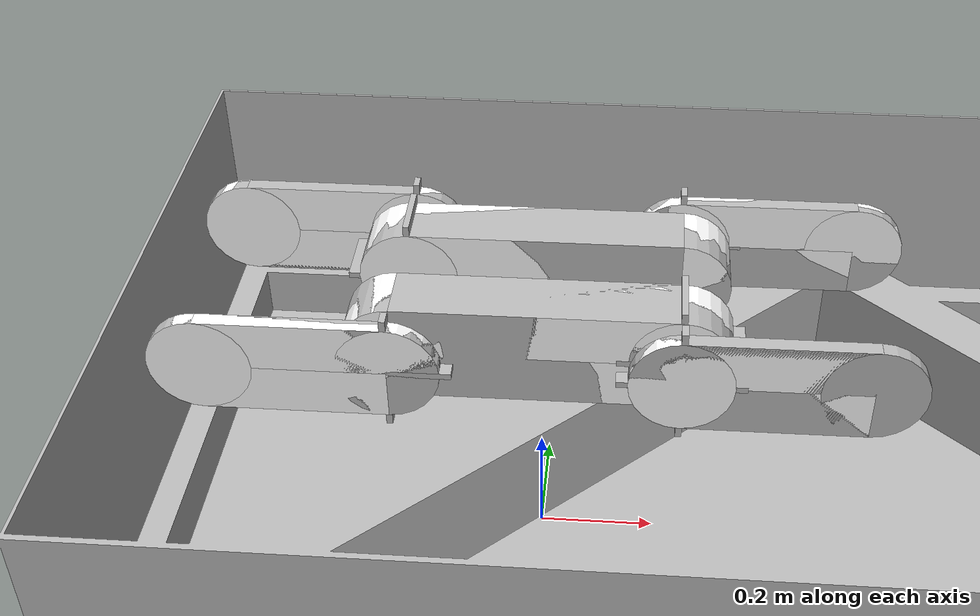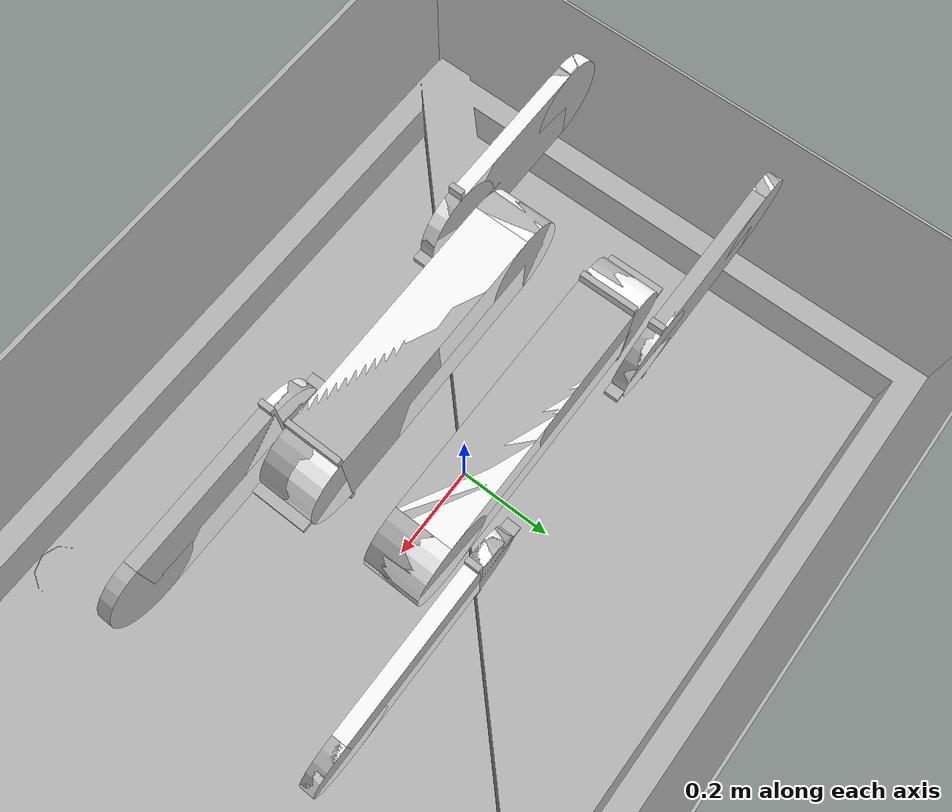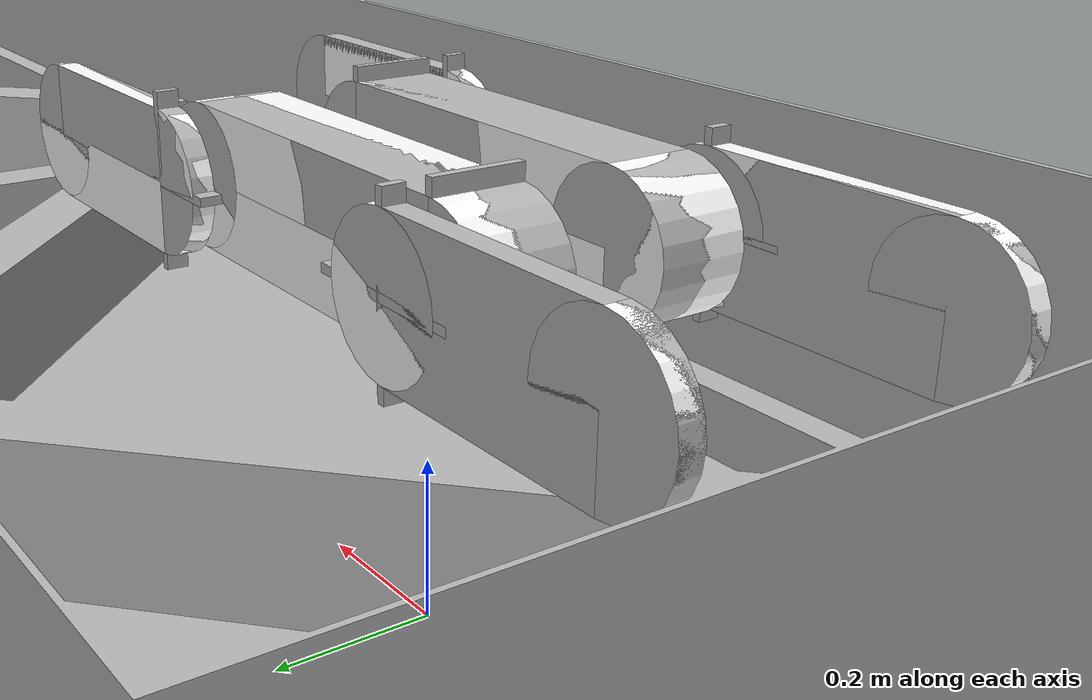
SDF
<sdf version="1.7">
 <world name="sample">
  <light name="sun" type="directional">
   <pose>0 0 10 0 -0 0</pose>
   <diffuse>0.8 0.8 0.8 1</diffuse>
   <specular>0.2 0.2 0.2 1</specular>
   <attenuation>
    <range>1000</range>
    <constant>0.9</constant>
    <linear>0.01</linear>
    <quadratic>0.001</quadratic>
   </attenuation>
   <direction>-0.5 0.1 -0.9</direction>
   <spot><inner_angle>0</inner_angle><outer_angle>0</outer_angle><falloff>0</falloff></spot>
  </light>
  <model name="ground_plane">
   <static>1</static>
   <link name="link">
    <collision name="collision">
     <geometry><plane><normal>0 0 1</normal><size>100 100</size></plane></geometry>
     <surface>
      <contact><collide_bitmask>65535</collide_bitmask></contact>
      <friction><ode><mu>100</mu><mu2>50</mu2></ode></friction>
     </surface>
    </collision>
    <visual name="visual">
     <cast_shadows>0</cast_shadows>
     <geometry><plane><normal>0 0 1</normal><size>100 100</size></plane></geometry>
     <material>
      <script><uri>file://media/materials/scripts/gazebo.material</uri><name>Gazebo/Grey</name></script>
     </material>
    </visual>
   </link>
  </model>
  <gravity>0 0 -9.8</gravity>
  <magnetic_field>6e-06 2.3e-05 -4.2e-05</magnetic_field>
  <atmosphere type="adiabatic"/>
  <physics type="ode">
   <max_step_size>0.001</max_step_size>
   <real_time_factor>1</real_time_factor>
   <real_time_update_rate>1000</real_time_update_rate>
  </physics>
  <scene><ambient>0.4 0.4 0.4 1</ambient><background>0.7 0.7 0.7 1</background><shadows>1</shadows></scene>
  <spherical_coordinates>
   <surface_model>EARTH_WGS84</surface_model>
   <latitude_deg>0</latitude_deg>
   <longitude_deg>0</longitude_deg>
   <elevation>0</elevation>
   <heading_deg>0</heading_deg>
  </spherical_coordinates>
  <model name="crawler">
   <link name="base_footprint">
    <inertial>
     <mass>60.4</mass>
     <inertia>
      <ixx>0.783006</ixx>
      <ixy>-0.009</ixy>
      <ixz>0</ixz>
      <iyy>1.16209</iyy>
      <iyz>0</iyz>
      <izz>1.68776</izz>
     </inertia>
    </inertial>
    <collision name="base_footprint_fixed_joint_lump__main_body_left_collision">
     <pose>0 0.1 0 0 -0 3.14159</pose>
     <geometry><box><size>0.45 0.1 0.164</size></box></geometry>
    </collision>
    <collision name="base_footprint_fixed_joint_lump__idler_left_collision_1">
     <pose>0.225 0.1 0 1.5708 -0 3.14159</pose>
     <geometry><cylinder><length>0.1</length><radius>0.082</radius></cylinder></geometry>
    </collision>
    <collision name="base_footprint_fixed_joint_lump__main_body_right_collision_2">
     <pose>0 -0.1 0 0 0 -3.14159</pose>
     <geometry><box><size>0.45 0.1 0.164</size></box></geometry>
    </collision>
    <collision name="base_footprint_fixed_joint_lump__idler_right_collision_3">
     <pose>-0.225 -0.1 0 1.5708 -0 -3.14159</pose>
     <geometry><cylinder><length>0.1</length><radius>0.082</radius></cylinder></geometry>
    </collision>
    <visual name="base_footprint_fixed_joint_lump__main_body_left_visual">
     <pose>0 0.1 0 0 -0 3.14159</pose>
     <geometry><box><size>0.45 0.1 0.164</size></box></geometry>
    </visual>
    <visual name="base_footprint_fixed_joint_lump__idler_left_visual_1">
     <pose>0.225 0.1 0 1.5708 -0 3.14159</pose>
     <geometry><cylinder><length>0.1</length><radius>0.082</radius></cylinder></geometry>
    </visual>
    <visual name="base_footprint_fixed_joint_lump__main_body_right_visual_2">
     <pose>0 -0.1 0 0 0 -3.14159</pose>
     <geometry><box><size>0.45 0.1 0.164</size></box></geometry>
    </visual>
    <visual name="base_footprint_fixed_joint_lump__idler_right_visual_3">
     <pose>-0.225 -0.1 0 1.5708 -0 -3.14159</pose>
     <geometry><cylinder><length>0.1</length><radius>0.082</radius></cylinder></geometry>
    </visual>
   </link>
   <joint name="sprocket_axle_left" type="revolute">
    <pose relative_to="base_footprint">-0.225 0.1 0 0 -0 3.14159</pose>
    <parent>base_footprint</parent>
    <child>sprocket_left</child>
    <axis>
     <xyz>0 -1 0</xyz>
     <limit><lower>-1e+16</lower><upper>1e+16</upper></limit>
     <dynamics><spring_reference>0</spring_reference><spring_stiffness>0</spring_stiffness></dynamics>
    </axis>
   </joint>
   <link name="sprocket_left">
    <pose relative_to="sprocket_axle_left">0 0 0 0 -0 0</pose>
    <inertial>
     <mass>0.2</mass>
     <inertia>
      <ixx>0.000502867</ixx>
      <ixy>0</ixy>
      <ixz>0</ixz>
      <iyy>0.0006724</iyy>
      <iyz>0</iyz>
      <izz>0.000502867</izz>
     </inertia>
    </inertial>
    <visual name="sprocket_left_visual">
     <pose>0 0 0 1.5708 -0 0</pose>
     <geometry><cylinder><length>0.1</length><radius>0.082</radius></cylinder></geometry>
    </visual>
    <visual name="sprocket_left_visual_1"><geometry><box><size>0.01 0.1 0.2</size></box></geometry></visual>
    <visual name="sprocket_left_visual_2"><geometry><box><size>0.2 0.1 0.01</size></box></geometry></visual>
   </link>
   <joint name="sprocket_axle_right" type="revolute">
    <pose relative_to="base_footprint">0.225 -0.1 0 0 0 -3.14159</pose>
    <parent>base_footprint</parent>
    <child>sprocket_right</child>
    <axis>
     <xyz>0 1 0</xyz>
     <limit><lower>-1e+16</lower><upper>1e+16</upper></limit>
     <dynamics><spring_reference>0</spring_reference><spring_stiffness>0</spring_stiffness></dynamics>
    </axis>
   </joint>
   <link name="sprocket_right">
    <pose relative_to="sprocket_axle_right">0 0 0 0 -0 0</pose>
    <inertial>
     <mass>0.2</mass>
     <inertia>
      <ixx>0.000502867</ixx>
      <ixy>0</ixy>
      <ixz>0</ixz>
      <iyy>0.0006724</iyy>
      <iyz>0</iyz>
      <izz>0.000502867</izz>
     </inertia>
    </inertial>
    <visual name="sprocket_right_visual">
     <pose>0 0 0 1.5708 -0 0</pose>
     <geometry><cylinder><length>0.1</length><radius>0.082</radius></cylinder></geometry>
    </visual>
    <visual name="sprocket_right_visual_1"><geometry><box><size>0.01 0.1 0.2</size></box></geometry></visual>
    <visual name="sprocket_right_visual_2"><geometry><box><size>0.2 0.1 0.01</size></box></geometry></visual>
   </link>
   <joint name="joint_left_front" type="revolute">
    <pose relative_to="base_footprint">0.225 0.188 0 3.14159 -0 0</pose>
    <parent>base_footprint</parent>
    <child>left_front</child>
    <axis>
     <xyz>0 1 0</xyz>
     <limit><lower>-2.35619</lower><upper>2.35619</upper><effort>10000</effort><velocity>1</velocity></limit>
     <dynamics><spring_reference>0</spring_reference><spring_stiffness>0</spring_stiffness></dynamics>
    </axis>
   </joint>
   <link name="left_front">
    <pose relative_to="joint_left_front">0 0 0 0 -0 0</pose>
    <inertial>
     <pose>0.10875 0 0 0 -0 0</pose>
     <mass>3.2</mass>
     <inertia>
      <ixx>0.00722687</ixx>
      <ixy>0</ixy>
      <ixz>0</ixz>
      <iyy>0.0441901</iyy>
      <iyz>0</iyz>
      <izz>0.0372966</izz>
     </inertia>
    </inertial>
    <collision name="left_front_fixed_joint_lump__flipper_body_left_front_collision">
     <pose>0.145 0 0 0 -0 0</pose>
     <geometry><box><size>0.29 0.025 0.164</size></box></geometry>
    </collision>
    <visual name="left_front_fixed_joint_lump__flipper_body_left_front_visual">
     <pose>0.145 0 0 0 -0 0</pose>
     <geometry><box><size>0.29 0.025 0.164</size></box></geometry>
    </visual>
    <visual name="left_front_fixed_joint_lump__flipper_idler_left_front_visual_1">
     <pose>0.29 0 0 1.5708 -0 0</pose>
     <geometry><cylinder><length>0.025</length><radius>0.082</radius></cylinder></geometry>
    </visual>
   </link>
   <joint name="flipper_sprocket_axle_left_front" type="revolute">
    <pose relative_to="left_front">0 0 0 0 -0 0</pose>
    <parent>left_front</parent>
    <child>flipper_sprocket_left_front</child>
    <axis>
     <xyz>0 1 0</xyz>
     <limit><lower>-1e+16</lower><upper>1e+16</upper></limit>
     <dynamics><spring_reference>0</spring_reference><spring_stiffness>0</spring_stiffness></dynamics>
    </axis>
   </joint>
   <link name="flipper_sprocket_left_front">
    <pose relative_to="flipper_sprocket_axle_left_front">0 0 0 0 -0 0</pose>
    <inertial>
     <mass>2</mass>
     <inertia>
      <ixx>0.00346617</ixx>
      <ixy>0</ixy>
      <ixz>0</ixz>
      <iyy>0.006724</iyy>
      <iyz>0</iyz>
      <izz>0.00346617</izz>
     </inertia>
    </inertial>
    <collision name="flipper_sprocket_left_front_collision">
     <pose>0 0 0 1.5708 -0 0</pose>
     <geometry><cylinder><length>0.025</length><radius>0.072</radius></cylinder></geometry>
    </collision>
    <visual name="flipper_sprocket_left_front_visual">
     <pose>0 0 0 1.5708 -0 0</pose>
     <geometry><cylinder><length>0.025</length><radius>0.082</radius></cylinder></geometry>
    </visual>
    <visual name="flipper_sprocket_left_front_visual_1">
     <geometry><box><size>0.01 0.025 0.2</size></box></geometry>
    </visual>
    <visual name="flipper_sprocket_left_front_visual_2">
     <geometry><box><size>0.2 0.025 0.01</size></box></geometry>
    </visual>
   </link>
   <joint name="joint_left_rear" type="revolute">
    <pose relative_to="base_footprint">-0.225 0.188 0 0 -0 3.14159</pose>
    <parent>base_footprint</parent>
    <child>left_rear</child>
    <axis>
     <xyz>0 -1 0</xyz>
     <limit><lower>-2.35619</lower><upper>2.35619</upper><effort>10000</effort><velocity>1</velocity></limit>
     <dynamics><spring_reference>0</spring_reference><spring_stiffness>0</spring_stiffness></dynamics>
    </axis>
   </joint>
   <link name="left_rear">
    <pose relative_to="joint_left_rear">0 0 0 0 -0 0</pose>
    <inertial>
     <pose>0.10875 0 0 0 -0 0</pose>
     <mass>3.2</mass>
     <inertia>
      <ixx>0.00722687</ixx>
      <ixy>0</ixy>
      <ixz>0</ixz>
      <iyy>0.0441901</iyy>
      <iyz>0</iyz>
      <izz>0.0372966</izz>
     </inertia>
    </inertial>
    <collision name="left_rear_fixed_joint_lump__flipper_body_left_rear_collision">
     <pose>0.145 0 0 0 -0 0</pose>
     <geometry><box><size>0.29 0.025 0.164</size></box></geometry>
    </collision>
    <visual name="left_rear_fixed_joint_lump__flipper_body_left_rear_visual">
     <pose>0.145 0 0 0 -0 0</pose>
     <geometry><box><size>0.29 0.025 0.164</size></box></geometry>
    </visual>
    <visual name="left_rear_fixed_joint_lump__flipper_idler_left_rear_visual_1">
     <pose>0.29 0 0 1.5708 -0 0</pose>
     <geometry><cylinder><length>0.025</length><radius>0.082</radius></cylinder></geometry>
    </visual>
   </link>
   <joint name="flipper_sprocket_axle_left_rear" type="revolute">
    <pose relative_to="left_rear">0 0 0 0 -0 0</pose>
    <parent>left_rear</parent>
    <child>flipper_sprocket_left_rear</child>
    <axis>
     <xyz>0 1 0</xyz>
     <limit><lower>-1e+16</lower><upper>1e+16</upper></limit>
     <dynamics><spring_reference>0</spring_reference><spring_stiffness>0</spring_stiffness></dynamics>
    </axis>
   </joint>
   <link name="flipper_sprocket_left_rear">
    <pose relative_to="flipper_sprocket_axle_left_rear">0 0 0 0 -0 0</pose>
    <inertial>
     <mass>2</mass>
     <inertia>
      <ixx>0.00346617</ixx>
      <ixy>0</ixy>
      <ixz>0</ixz>
      <iyy>0.006724</iyy>
      <iyz>0</iyz>
      <izz>0.00346617</izz>
     </inertia>
    </inertial>
    <collision name="flipper_sprocket_left_rear_collision">
     <pose>0 0 0 1.5708 -0 0</pose>
     <geometry><cylinder><length>0.025</length><radius>0.072</radius></cylinder></geometry>
    </collision>
    <visual name="flipper_sprocket_left_rear_visual">
     <pose>0 0 0 1.5708 -0 0</pose>
     <geometry><cylinder><length>0.025</length><radius>0.082</radius></cylinder></geometry>
    </visual>
    <visual name="flipper_sprocket_left_rear_visual_1">
     <geometry><box><size>0.01 0.025 0.2</size></box></geometry>
    </visual>
    <visual name="flipper_sprocket_left_rear_visual_2">
     <geometry><box><size>0.2 0.025 0.01</size></box></geometry>
    </visual>
   </link>
   <joint name="joint_right_front" type="revolute">
    <pose relative_to="base_footprint">0.225 -0.188 0 0 -0 0</pose>
    <parent>base_footprint</parent>
    <child>right_front</child>
    <axis>
     <xyz>0 -1 0</xyz>
     <limit><lower>-2.35619</lower><upper>2.35619</upper><effort>10000</effort><velocity>1</velocity></limit>
     <dynamics><spring_reference>0</spring_reference><spring_stiffness>0</spring_stiffness></dynamics>
    </axis>
   </joint>
   <link name="right_front">
    <pose relative_to="joint_right_front">0 0 0 0 -0 0</pose>
    <inertial>
     <pose>0.10875 0 0 0 -0 0</pose>
     <mass>3.2</mass>
     <inertia>
      <ixx>0.00722687</ixx>
      <ixy>0</ixy>
      <ixz>0</ixz>
      <iyy>0.0441901</iyy>
      <iyz>0</iyz>
      <izz>0.0372966</izz>
     </inertia>
    </inertial>
    <collision name="right_front_fixed_joint_lump__flipper_body_right_front_collision">
     <pose>0.145 0 0 0 -0 0</pose>
     <geometry><box><size>0.29 0.025 0.164</size></box></geometry>
    </collision>
    <visual name="right_front_fixed_joint_lump__flipper_body_right_front_visual">
     <pose>0.145 0 0 0 -0 0</pose>
     <geometry><box><size>0.29 0.025 0.164</size></box></geometry>
    </visual>
    <visual name="right_front_fixed_joint_lump__flipper_idler_right_front_visual_1">
     <pose>0.29 0 0 1.5708 -0 0</pose>
     <geometry><cylinder><length>0.025</length><radius>0.082</radius></cylinder></geometry>
    </visual>
   </link>
   <joint name="flipper_sprocket_axle_right_front" type="revolute">
    <pose relative_to="right_front">0 0 0 0 -0 0</pose>
    <parent>right_front</parent>
    <child>flipper_sprocket_right_front</child>
    <axis>
     <xyz>0 1 0</xyz>
     <limit><lower>-1e+16</lower><upper>1e+16</upper></limit>
     <dynamics><spring_reference>0</spring_reference><spring_stiffness>0</spring_stiffness></dynamics>
    </axis>
   </joint>
   <link name="flipper_sprocket_right_front">
    <pose relative_to="flipper_sprocket_axle_right_front">0 0 0 0 -0 0</pose>
    <inertial>
     <mass>2</mass>
     <inertia>
      <ixx>0.00346617</ixx>
      <ixy>0</ixy>
      <ixz>0</ixz>
      <iyy>0.006724</iyy>
      <iyz>0</iyz>
      <izz>0.00346617</izz>
     </inertia>
    </inertial>
    <collision name="flipper_sprocket_right_front_collision">
     <pose>0 0 0 1.5708 -0 0</pose>
     <geometry><cylinder><length>0.025</length><radius>0.072</radius></cylinder></geometry>
    </collision>
    <visual name="flipper_sprocket_right_front_visual">
     <pose>0 0 0 1.5708 -0 0</pose>
     <geometry><cylinder><length>0.025</length><radius>0.082</radius></cylinder></geometry>
    </visual>
    <visual name="flipper_sprocket_right_front_visual_1">
     <geometry><box><size>0.01 0.025 0.2</size></box></geometry>
    </visual>
    <visual name="flipper_sprocket_right_front_visual_2">
     <geometry><box><size>0.2 0.025 0.01</size></box></geometry>
    </visual>
   </link>
   <joint name="joint_right_rear" type="revolute">
    <pose relative_to="base_footprint">-0.225 -0.188 0 3.14159 -0 3.14159</pose>
    <parent>base_footprint</parent>
    <child>right_rear</child>
    <axis>
     <xyz>0 1 0</xyz>
     <limit><lower>-2.35619</lower><upper>2.35619</upper><effort>10000</effort><velocity>1</velocity></limit>
     <dynamics><spring_reference>0</spring_reference><spring_stiffness>0</spring_stiffness></dynamics>
    </axis>
   </joint>
   <link name="right_rear">
    <pose relative_to="joint_right_rear">0 0 0 0 -0 0</pose>
    <inertial>
     <pose>0.10875 0 0 0 -0 0</pose>
     <mass>3.2</mass>
     <inertia>
      <ixx>0.00722687</ixx>
      <ixy>0</ixy>
      <ixz>0</ixz>
      <iyy>0.0441901</iyy>
      <iyz>0</iyz>
      <izz>0.0372966</izz>
     </inertia>
    </inertial>
    <collision name="right_rear_fixed_joint_lump__flipper_body_right_rear_collision">
     <pose>0.145 0 0 0 -0 0</pose>
     <geometry><box><size>0.29 0.025 0.164</size></box></geometry>
    </collision>
    <visual name="right_rear_fixed_joint_lump__flipper_body_right_rear_visual">
     <pose>0.145 0 0 0 -0 0</pose>
     <geometry><box><size>0.29 0.025 0.164</size></box></geometry>
    </visual>
    <visual name="right_rear_fixed_joint_lump__flipper_idler_right_rear_visual_1">
     <pose>0.29 0 0 1.5708 -0 0</pose>
     <geometry><cylinder><length>0.025</length><radius>0.082</radius></cylinder></geometry>
    </visual>
   </link>
   <joint name="flipper_sprocket_axle_right_rear" type="revolute">
    <pose relative_to="right_rear">0 0 0 0 -0 0</pose>
    <parent>right_rear</parent>
    <child>flipper_sprocket_right_rear</child>
    <axis>
     <xyz>0 1 0</xyz>
     <limit><lower>-1e+16</lower><upper>1e+16</upper></limit>
     <dynamics><spring_reference>0</spring_reference><spring_stiffness>0</spring_stiffness></dynamics>
    </axis>
   </joint>
   <link name="flipper_sprocket_right_rear">
    <pose relative_to="flipper_sprocket_axle_right_rear">0 0 0 0 -0 0</pose>
    <inertial>
     <mass>2</mass>
     <inertia>
      <ixx>0.00346617</ixx>
      <ixy>0</ixy>
      <ixz>0</ixz>
      <iyy>0.006724</iyy>
      <iyz>0</iyz>
      <izz>0.00346617</izz>
     </inertia>
    </inertial>
    <collision name="flipper_sprocket_right_rear_collision">
     <pose>0 0 0 1.5708 -0 0</pose>
     <geometry><cylinder><length>0.025</length><radius>0.072</radius></cylinder></geometry>
    </collision>
    <visual name="flipper_sprocket_right_rear_visual">
     <pose>0 0 0 1.5708 -0 0</pose>
     <geometry><cylinder><length>0.025</length><radius>0.082</radius></cylinder></geometry>
    </visual>
    <visual name="flipper_sprocket_right_rear_visual_1">
     <geometry><box><size>0.01 0.025 0.2</size></box></geometry>
    </visual>
    <visual name="flipper_sprocket_right_rear_visual_2">
     <geometry><box><size>0.2 0.025 0.01</size></box></geometry>
    </visual>
   </link>
   <link name="track_left_straight_segment_link0">
    <pose>-0.225 0.1 0.082 0 -0 0</pose>
    <inertial>
     <pose>0.225 0 -0.041 0 -0 0</pose>
     <mass>0.1</mass>
     <inertia>
      <ixx>0.000139367</ixx>
      <ixy>0</ixy>
      <ixz>0</ixz>
      <iyy>0.00174353</iyy>
      <iyz>0</iyz>
      <izz>0.00177083</izz>
     </inertia>
    </inertial>
    <collision name="collision">
     <pose>0.225 0 -0.041 0 -0 0</pose>
     <geometry><box><size>0.45 0.1 0.082</size></box></geometry>
     <surface>
      <friction><ode><mu>0.5</mu><mu2>0.5</mu2></ode></friction>
      <contact><ode><min_depth>0.01</min_depth></ode></contact>
     </surface>
    </collision>
    <visual name="visual">
     <pose>0.225 0 -0.041 0 -0 0</pose>
     <geometry><box><size>0.45 0.1 0.082</size></box></geometry>
     <material>
      <ambient>1 1 1 1</ambient>
      <diffuse>1 1 1 1</diffuse>
      <specular>0 0 0 1</specular>
      <emissive>0 0 0 1</emissive>
     </material>
    </visual>
   </link>
   <link name="track_left_straight_segment_link1">
    <pose>0.225 0.1 -0.082 3.14159 -0 3.14159</pose>
    <inertial>
     <pose>0.225 0 -0.041 0 -0 0</pose>
     <mass>0.1</mass>
     <inertia>
      <ixx>0.000139367</ixx>
      <ixy>0</ixy>
      <ixz>0</ixz>
      <iyy>0.00174353</iyy>
      <iyz>0</iyz>
      <izz>0.00177083</izz>
     </inertia>
    </inertial>
    <collision name="collision">
     <pose>0.225 0 -0.041 0 -0 0</pose>
     <geometry><box><size>0.45 0.1 0.082</size></box></geometry>
     <surface>
      <friction><ode><mu>0.5</mu><mu2>0.5</mu2></ode></friction>
      <contact><ode><min_depth>0.01</min_depth></ode></contact>
     </surface>
    </collision>
    <visual name="visual">
     <pose>0.225 0 -0.041 0 -0 0</pose>
     <geometry><box><size>0.45 0.1 0.082</size></box></geometry>
     <material>
      <ambient>1 1 1 1</ambient>
      <diffuse>1 1 1 1</diffuse>
      <specular>0 0 0 1</specular>
      <emissive>0 0 0 1</emissive>
     </material>
    </visual>
   </link>
   <joint name="track_left_straight_segment_joint0" type="prismatic">
    <child>track_left_straight_segment_link0</child>
    <axis>
     <xyz>1 0 0</xyz>
     <limit><lower>-1e+16</lower><upper>1e+16</upper></limit>
     <dynamics><spring_reference>0</spring_reference><spring_stiffness>0</spring_stiffness></dynamics>
     <use_parent_model_frame>0</use_parent_model_frame>
    </axis>
    <physics>
     <ode><implicit_spring_damper>1</implicit_spring_damper><limit><cfm>0</cfm><erp>0.2</erp></limit></ode>
    </physics>
    <parent>base_footprint</parent>
   </joint>
   <joint name="track_left_straight_segment_joint1" type="prismatic">
    <child>track_left_straight_segment_link1</child>
    <axis>
     <xyz>1 0 0</xyz>
     <limit><lower>-1e+16</lower><upper>1e+16</upper></limit>
     <dynamics><spring_reference>0</spring_reference><spring_stiffness>0</spring_stiffness></dynamics>
     <use_parent_model_frame>0</use_parent_model_frame>
    </axis>
    <physics>
     <ode><implicit_spring_damper>1</implicit_spring_damper><limit><cfm>0</cfm><erp>0.2</erp></limit></ode>
    </physics>
    <parent>base_footprint</parent>
   </joint>
   <link name="track_left_arc_segment_link0">
    <pose>0.225 0.1 0.082 0 -0 0</pose>
    <inertial>
     <pose>0 0 -0.082 1.5708 -0 0</pose>
     <mass>0.1</mass>
     <inertia>
      <ixx>0.000251433</ixx>
      <ixy>0</ixy>
      <ixz>0</ixz>
      <iyy>0.000251433</iyy>
      <iyz>0</iyz>
      <izz>0.0003362</izz>
     </inertia>
    </inertial>
    <collision name="collision">
     <pose>0 0 -0.082 1.5708 -0 0</pose>
     <geometry><cylinder><length>0.1</length><radius>0.082</radius></cylinder></geometry>
     <surface>
      <friction><ode><mu>0.5</mu><mu2>0.5</mu2></ode></friction>
      <contact><ode><min_depth>0.01</min_depth></ode></contact>
     </surface>
    </collision>
    <visual name="visual">
     <pose>0 0 -0.082 1.5708 -0 0</pose>
     <geometry><cylinder><length>0.1</length><radius>0.082</radius></cylinder></geometry>
     <material>
      <ambient>1 1 1 1</ambient>
      <diffuse>1 1 1 1</diffuse>
      <specular>0 0 0 1</specular>
      <emissive>0 0 0 1</emissive>
     </material>
    </visual>
   </link>
   <link name="track_left_arc_segment_link1">
    <pose>-0.225 0.1 -0.082 3.14159 -0 3.14159</pose>
    <inertial>
     <pose>0 0 -0.082 1.5708 -0 0</pose>
     <mass>0.1</mass>
     <inertia>
      <ixx>0.000251433</ixx>
      <ixy>0</ixy>
      <ixz>0</ixz>
      <iyy>0.000251433</iyy>
      <iyz>0</iyz>
      <izz>0.0003362</izz>
     </inertia>
    </inertial>
    <collision name="collision">
     <pose>0 0 -0.082 1.5708 -0 0</pose>
     <geometry><cylinder><length>0.1</length><radius>0.082</radius></cylinder></geometry>
     <surface>
      <friction><ode><mu>0.5</mu><mu2>0.5</mu2></ode></friction>
      <contact><ode><min_depth>0.01</min_depth></ode></contact>
     </surface>
    </collision>
    <visual name="visual">
     <pose>0 0 -0.082 1.5708 -0 0</pose>
     <geometry><cylinder><length>0.1</length><radius>0.082</radius></cylinder></geometry>
     <material>
      <ambient>1 1 1 1</ambient>
      <diffuse>1 1 1 1</diffuse>
      <specular>0 0 0 1</specular>
      <emissive>0 0 0 1</emissive>
     </material>
    </visual>
   </link>
   <joint name="track_left_arc_segment_joint0" type="revolute">
    <child>track_left_arc_segment_link0</child>
    <pose>0 0 -0.082 0 -0 0</pose>
    <axis>
     <xyz>0 1 0</xyz>
     <limit><lower>-1e+16</lower><upper>1e+16</upper></limit>
     <dynamics><spring_reference>0</spring_reference><spring_stiffness>0</spring_stiffness></dynamics>
     <use_parent_model_frame>0</use_parent_model_frame>
    </axis>
    <physics>
     <ode><implicit_spring_damper>1</implicit_spring_damper><limit><cfm>0</cfm><erp>0.2</erp></limit></ode>
    </physics>
    <parent>base_footprint</parent>
   </joint>
   <joint name="track_left_arc_segment_joint1" type="revolute">
    <child>track_left_arc_segment_link1</child>
    <pose>0 0 -0.082 0 -0 0</pose>
    <axis>
     <xyz>0 1 0</xyz>
     <limit><lower>-1e+16</lower><upper>1e+16</upper></limit>
     <dynamics><spring_reference>0</spring_reference><spring_stiffness>0</spring_stiffness></dynamics>
     <use_parent_model_frame>0</use_parent_model_frame>
    </axis>
    <physics>
     <ode><implicit_spring_damper>1</implicit_spring_damper><limit><cfm>0</cfm><erp>0.2</erp></limit></ode>
    </physics>
    <parent>base_footprint</parent>
   </joint>
   <plugin name="track_left" filename="libContinuousTrack.so">
    <sprocket><joint>sprocket_axle_left</joint><pitch_diameter>0.24</pitch_diameter></sprocket>
    <trajectory>
     <segment><joint>track_left_straight_segment_joint0</joint><end_position>0.45</end_position></segment>
     <segment><joint>track_left_arc_segment_joint0</joint><end_position>3.141592653589793</end_position></segment>
     <segment><joint>track_left_straight_segment_joint1</joint><end_position>0.45</end_position></segment>
     <segment><joint>track_left_arc_segment_joint1</joint><end_position>3.141592653589793</end_position></segment>
    </trajectory>
    <pattern>
     <elements_per_round>20</elements_per_round>
     <element>
      <collision name="collision">
       <geometry><box><size>0.02 0.1 0.02</size></box></geometry>
       <surface>
        <friction><ode><mu>0.5</mu><mu2>0.5</mu2></ode></friction>
        <contact><ode><min_depth>0.01</min_depth></ode></contact>
       </surface>
      </collision>
      <visual name="visual">
       <geometry><box><size>0.02 0.1 0.02</size></box></geometry>
       <material>
        <ambient>1 1 1 1</ambient>
        <diffuse>1 1 1 1</diffuse>
        <specular>0 0 0 1</specular>
        <emissive>0 0 0 1</emissive>
       </material>
      </visual>
     </element>
     <element>
      <collision name="collision">
       <pose>0 0.05 0 1.5707963267948966 0 0</pose>
       <geometry>
        <polyline>
         <point>-0.02 -0.01</point>
         <point>-0.01 0.01</point>
         <point>0.01 0.01</point>
         <point>0.02 -0.01</point>
         <height>0.1</height>
        </polyline>
       </geometry>
       <surface>
        <friction><ode><mu>0.5</mu><mu2>0.5</mu2></ode></friction>
        <contact><ode><min_depth>0.01</min_depth></ode></contact>
       </surface>
      </collision>
      <visual name="visual">
       <pose>0 0.05 0 1.5707963267948966 0 0</pose>
       <geometry>
        <polyline>
         <point>-0.02 -0.01</point>
         <point>-0.01 0.01</point>
         <point>0.01 0.01</point>
         <point>0.02 -0.01</point>
         <height>0.1</height>
        </polyline>
       </geometry>
       <material>
        <ambient>1 1 1 1</ambient>
        <diffuse>1 1 1 1</diffuse>
        <specular>0 0 0 1</specular>
        <emissive>0 0 0 1</emissive>
       </material>
      </visual>
     </element>
    </pattern>
    <robotNamespace>/</robotNamespace>
   </plugin>
   <link name="track_right_straight_segment_link0">
    <pose>-0.225 -0.1 0.082 0 -0 0</pose>
    <inertial>
     <pose>0.225 0 -0.041 0 -0 0</pose>
     <mass>0.1</mass>
     <inertia>
      <ixx>0.000139367</ixx>
      <ixy>0</ixy>
      <ixz>0</ixz>
      <iyy>0.00174353</iyy>
      <iyz>0</iyz>
      <izz>0.00177083</izz>
     </inertia>
    </inertial>
    <collision name="collision">
     <pose>0.225 0 -0.041 0 -0 0</pose>
     <geometry><box><size>0.45 0.1 0.082</size></box></geometry>
     <surface>
      <friction><ode><mu>0.5</mu><mu2>0.5</mu2></ode></friction>
      <contact><ode><min_depth>0.01</min_depth></ode></contact>
     </surface>
    </collision>
    <visual name="visual">
     <pose>0.225 0 -0.041 0 -0 0</pose>
     <geometry><box><size>0.45 0.1 0.082</size></box></geometry>
     <material>
      <ambient>1 1 1 1</ambient>
      <diffuse>1 1 1 1</diffuse>
      <specular>0 0 0 1</specular>
      <emissive>0 0 0 1</emissive>
     </material>
    </visual>
   </link>
   <link name="track_right_straight_segment_link1">
    <pose>0.225 -0.1 -0.082 3.14159 -0 3.14159</pose>
    <inertial>
     <pose>0.225 0 -0.041 0 -0 0</pose>
     <mass>0.1</mass>
     <inertia>
      <ixx>0.000139367</ixx>
      <ixy>0</ixy>
      <ixz>0</ixz>
      <iyy>0.00174353</iyy>
      <iyz>0</iyz>
      <izz>0.00177083</izz>
     </inertia>
    </inertial>
    <collision name="collision">
     <pose>0.225 0 -0.041 0 -0 0</pose>
     <geometry><box><size>0.45 0.1 0.082</size></box></geometry>
     <surface>
      <friction><ode><mu>0.5</mu><mu2>0.5</mu2></ode></friction>
      <contact><ode><min_depth>0.01</min_depth></ode></contact>
     </surface>
    </collision>
    <visual name="visual">
     <pose>0.225 0 -0.041 0 -0 0</pose>
     <geometry><box><size>0.45 0.1 0.082</size></box></geometry>
     <material>
      <ambient>1 1 1 1</ambient>
      <diffuse>1 1 1 1</diffuse>
      <specular>0 0 0 1</specular>
      <emissive>0 0 0 1</emissive>
     </material>
    </visual>
   </link>
   <joint name="track_right_straight_segment_joint0" type="prismatic">
    <child>track_right_straight_segment_link0</child>
    <axis>
     <xyz>1 0 0</xyz>
     <limit><lower>-1e+16</lower><upper>1e+16</upper></limit>
     <dynamics><spring_reference>0</spring_reference><spring_stiffness>0</spring_stiffness></dynamics>
     <use_parent_model_frame>0</use_parent_model_frame>
    </axis>
    <physics>
     <ode><implicit_spring_damper>1</implicit_spring_damper><limit><cfm>0</cfm><erp>0.2</erp></limit></ode>
    </physics>
    <parent>base_footprint</parent>
   </joint>
   <joint name="track_right_straight_segment_joint1" type="prismatic">
    <child>track_right_straight_segment_link1</child>
    <axis>
     <xyz>1 0 0</xyz>
     <limit><lower>-1e+16</lower><upper>1e+16</upper></limit>
     <dynamics><spring_reference>0</spring_reference><spring_stiffness>0</spring_stiffness></dynamics>
     <use_parent_model_frame>0</use_parent_model_frame>
    </axis>
    <physics>
     <ode><implicit_spring_damper>1</implicit_spring_damper><limit><cfm>0</cfm><erp>0.2</erp></limit></ode>
    </physics>
    <parent>base_footprint</parent>
   </joint>
   <link name="track_right_arc_segment_link0">
    <pose>0.225 -0.1 0.082 0 -0 0</pose>
    <inertial>
     <pose>0 0 -0.082 1.5708 -0 0</pose>
     <mass>0.1</mass>
     <inertia>
      <ixx>0.000251433</ixx>
      <ixy>0</ixy>
      <ixz>0</ixz>
      <iyy>0.000251433</iyy>
      <iyz>0</iyz>
      <izz>0.0003362</izz>
     </inertia>
    </inertial>
    <collision name="collision">
     <pose>0 0 -0.082 1.5708 -0 0</pose>
     <geometry><cylinder><length>0.1</length><radius>0.082</radius></cylinder></geometry>
     <surface>
      <friction><ode><mu>0.5</mu><mu2>0.5</mu2></ode></friction>
      <contact><ode><min_depth>0.01</min_depth></ode></contact>
     </surface>
    </collision>
    <visual name="visual">
     <pose>0 0 -0.082 1.5708 -0 0</pose>
     <geometry><cylinder><length>0.1</length><radius>0.082</radius></cylinder></geometry>
     <material>
      <ambient>1 1 1 1</ambient>
      <diffuse>1 1 1 1</diffuse>
      <specular>0 0 0 1</specular>
      <emissive>0 0 0 1</emissive>
     </material>
    </visual>
   </link>
   <link name="track_right_arc_segment_link1">
    <pose>-0.225 -0.1 -0.082 3.14159 -0 3.14159</pose>
    <inertial>
     <pose>0 0 -0.082 1.5708 -0 0</pose>
     <mass>0.1</mass>
     <inertia>
      <ixx>0.000251433</ixx>
      <ixy>0</ixy>
      <ixz>0</ixz>
      <iyy>0.000251433</iyy>
      <iyz>0</iyz>
      <izz>0.0003362</izz>
     </inertia>
    </inertial>
    <collision name="collision">
     <pose>0 0 -0.082 1.5708 -0 0</pose>
     <geometry><cylinder><length>0.1</length><radius>0.082</radius></cylinder></geometry>
     <surface>
      <friction><ode><mu>0.5</mu><mu2>0.5</mu2></ode></friction>
      <contact><ode><min_depth>0.01</min_depth></ode></contact>
     </surface>
    </collision>
    <visual name="visual">
     <pose>0 0 -0.082 1.5708 -0 0</pose>
     <geometry><cylinder><length>0.1</length><radius>0.082</radius></cylinder></geometry>
     <material>
      <ambient>1 1 1 1</ambient>
      <diffuse>1 1 1 1</diffuse>
      <specular>0 0 0 1</specular>
      <emissive>0 0 0 1</emissive>
     </material>
    </visual>
   </link>
   <joint name="track_right_arc_segment_joint0" type="revolute">
    <child>track_right_arc_segment_link0</child>
    <pose>0 0 -0.082 0 -0 0</pose>
    <axis>
     <xyz>0 1 0</xyz>
     <limit><lower>-1e+16</lower><upper>1e+16</upper></limit>
     <dynamics><spring_reference>0</spring_reference><spring_stiffness>0</spring_stiffness></dynamics>
     <use_parent_model_frame>0</use_parent_model_frame>
    </axis>
    <physics>
     <ode><implicit_spring_damper>1</implicit_spring_damper><limit><cfm>0</cfm><erp>0.2</erp></limit></ode>
    </physics>
    <parent>base_footprint</parent>
   </joint>
   <joint name="track_right_arc_segment_joint1" type="revolute">
    <child>track_right_arc_segment_link1</child>
    <pose>0 0 -0.082 0 -0 0</pose>
    <axis>
     <xyz>0 1 0</xyz>
     <limit><lower>-1e+16</lower><upper>1e+16</upper></limit>
     <dynamics><spring_reference>0</spring_reference><spring_stiffness>0</spring_stiffness></dynamics>
     <use_parent_model_frame>0</use_parent_model_frame>
    </axis>
    <physics>
     <ode><implicit_spring_damper>1</implicit_spring_damper><limit><cfm>0</cfm><erp>0.2</erp></limit></ode>
    </physics>
    <parent>base_footprint</parent>
   </joint>
   <plugin name="track_right" filename="libContinuousTrack.so">
    <sprocket><joint>sprocket_axle_right</joint><pitch_diameter>0.24</pitch_diameter></sprocket>
    <trajectory>
     <segment><joint>track_right_straight_segment_joint0</joint><end_position>0.45</end_position></segment>
     <segment><joint>track_right_arc_segment_joint0</joint><end_position>3.141592653589793</end_position></segment>
     <segment><joint>track_right_straight_segment_joint1</joint><end_position>0.45</end_position></segment>
     <segment><joint>track_right_arc_segment_joint1</joint><end_position>3.141592653589793</end_position></segment>
    </trajectory>
    <pattern>
     <elements_per_round>20</elements_per_round>
     <element>
      <collision name="collision">
       <geometry><box><size>0.02 0.1 0.02</size></box></geometry>
       <surface>
        <friction><ode><mu>0.5</mu><mu2>0.5</mu2></ode></friction>
        <contact><ode><min_depth>0.01</min_depth></ode></contact>
       </surface>
      </collision>
      <visual name="visual">
       <geometry><box><size>0.02 0.1 0.02</size></box></geometry>
       <material>
        <ambient>1 1 1 1</ambient>
        <diffuse>1 1 1 1</diffuse>
        <specular>0 0 0 1</specular>
        <emissive>0 0 0 1</emissive>
       </material>
      </visual>
     </element>
     <element>
      <collision name="collision">
       <pose>0 0.05 0 1.5707963267948966 0 0</pose>
       <geometry>
        <polyline>
         <point>-0.02 -0.01</point>
         <point>-0.01 0.01</point>
         <point>0.01 0.01</point>
         <point>0.02 -0.01</point>
         <height>0.1</height>
        </polyline>
       </geometry>
       <surface>
        <friction><ode><mu>0.5</mu><mu2>0.5</mu2></ode></friction>
        <contact><ode><min_depth>0.01</min_depth></ode></contact>
       </surface>
      </collision>
      <visual name="visual">
       <pose>0 0.05 0 1.5707963267948966 0 0</pose>
       <geometry>
        <polyline>
         <point>-0.02 -0.01</point>
         <point>-0.01 0.01</point>
         <point>0.01 0.01</point>
         <point>0.02 -0.01</point>
         <height>0.1</height>
        </polyline>
       </geometry>
       <material>
        <ambient>1 1 1 1</ambient>
        <diffuse>1 1 1 1</diffuse>
        <specular>0 0 0 1</specular>
        <emissive>0 0 0 1</emissive>
       </material>
      </visual>
     </element>
    </pattern>
    <robotNamespace>/</robotNamespace>
   </plugin>
   <link name="flipper_track_left_front_straight_segment_link0">
    <pose>0.225 0.188 0.082 0 -0 0</pose>
    <inertial>
     <pose>0.145 0 -0.041 0 -0 0</pose>
     <mass>0.1</mass>
     <inertia>
      <ixx>6.12417e-05</ixx>
      <ixy>0</ixy>
      <ixz>0</ixz>
      <iyy>0.000756867</iyy>
      <iyz>0</iyz>
      <izz>0.000706042</izz>
     </inertia>
    </inertial>
    <collision name="collision">
     <pose>0.145 0 -0.041 0 -0 0</pose>
     <geometry><box><size>0.29 0.025 0.082</size></box></geometry>
     <surface>
      <friction><ode><mu>0.5</mu><mu2>0.5</mu2></ode></friction>
      <contact><ode><min_depth>0.01</min_depth></ode></contact>
     </surface>
    </collision>
    <visual name="visual">
     <pose>0.145 0 -0.041 0 -0 0</pose>
     <geometry><box><size>0.29 0.025 0.082</size></box></geometry>
     <material>
      <ambient>1 1 1 1</ambient>
      <diffuse>1 1 1 1</diffuse>
      <specular>0 0 0 1</specular>
      <emissive>0 0 0 1</emissive>
     </material>
    </visual>
   </link>
   <link name="flipper_track_left_front_straight_segment_link1">
    <pose>0.515 0.188 -0.082 3.14159 -0 3.14159</pose>
    <inertial>
     <pose>0.145 0 -0.041 0 -0 0</pose>
     <mass>0.1</mass>
     <inertia>
      <ixx>6.12417e-05</ixx>
      <ixy>0</ixy>
      <ixz>0</ixz>
      <iyy>0.000756867</iyy>
      <iyz>0</iyz>
      <izz>0.000706042</izz>
     </inertia>
    </inertial>
    <collision name="collision">
     <pose>0.145 0 -0.041 0 -0 0</pose>
     <geometry><box><size>0.29 0.025 0.082</size></box></geometry>
     <surface>
      <friction><ode><mu>0.5</mu><mu2>0.5</mu2></ode></friction>
      <contact><ode><min_depth>0.01</min_depth></ode></contact>
     </surface>
    </collision>
    <visual name="visual">
     <pose>0.145 0 -0.041 0 -0 0</pose>
     <geometry><box><size>0.29 0.025 0.082</size></box></geometry>
     <material>
      <ambient>1 1 1 1</ambient>
      <diffuse>1 1 1 1</diffuse>
      <specular>0 0 0 1</specular>
      <emissive>0 0 0 1</emissive>
     </material>
    </visual>
   </link>
   <joint name="flipper_track_left_front_straight_segment_joint0" type="prismatic">
    <child>flipper_track_left_front_straight_segment_link0</child>
    <axis>
     <xyz>1 0 0</xyz>
     <limit><lower>-1e+16</lower><upper>1e+16</upper></limit>
     <dynamics><spring_reference>0</spring_reference><spring_stiffness>0</spring_stiffness></dynamics>
     <use_parent_model_frame>0</use_parent_model_frame>
    </axis>
    <physics>
     <ode><implicit_spring_damper>1</implicit_spring_damper><limit><cfm>0</cfm><erp>0.2</erp></limit></ode>
    </physics>
    <parent>left_front</parent>
   </joint>
   <joint name="flipper_track_left_front_straight_segment_joint1" type="prismatic">
    <child>flipper_track_left_front_straight_segment_link1</child>
    <axis>
     <xyz>1 0 0</xyz>
     <limit><lower>-1e+16</lower><upper>1e+16</upper></limit>
     <dynamics><spring_reference>0</spring_reference><spring_stiffness>0</spring_stiffness></dynamics>
     <use_parent_model_frame>0</use_parent_model_frame>
    </axis>
    <physics>
     <ode><implicit_spring_damper>1</implicit_spring_damper><limit><cfm>0</cfm><erp>0.2</erp></limit></ode>
    </physics>
    <parent>left_front</parent>
   </joint>
   <link name="flipper_track_left_front_arc_segment_link0">
    <pose>0.515 0.188 0.082 0 -0 0</pose>
    <inertial>
     <pose>0 0 -0.082 1.5708 -0 0</pose>
     <mass>0.1</mass>
     <inertia>
      <ixx>0.000173308</ixx>
      <ixy>0</ixy>
      <ixz>0</ixz>
      <iyy>0.000173308</iyy>
      <iyz>0</iyz>
      <izz>0.0003362</izz>
     </inertia>
    </inertial>
    <collision name="collision">
     <pose>0 0 -0.082 1.5708 -0 0</pose>
     <geometry><cylinder><length>0.025</length><radius>0.082</radius></cylinder></geometry>
     <surface>
      <friction><ode><mu>0.5</mu><mu2>0.5</mu2></ode></friction>
      <contact><ode><min_depth>0.01</min_depth></ode></contact>
     </surface>
    </collision>
    <visual name="visual">
     <pose>0 0 -0.082 1.5708 -0 0</pose>
     <geometry><cylinder><length>0.025</length><radius>0.082</radius></cylinder></geometry>
     <material>
      <ambient>1 1 1 1</ambient>
      <diffuse>1 1 1 1</diffuse>
      <specular>0 0 0 1</specular>
      <emissive>0 0 0 1</emissive>
     </material>
    </visual>
   </link>
   <link name="flipper_track_left_front_arc_segment_link1">
    <pose>0.225 0.188 -0.082 3.14159 -0 3.14159</pose>
    <inertial>
     <pose>0 0 -0.082 1.5708 -0 0</pose>
     <mass>0.1</mass>
     <inertia>
      <ixx>0.000173308</ixx>
      <ixy>0</ixy>
      <ixz>0</ixz>
      <iyy>0.000173308</iyy>
      <iyz>0</iyz>
      <izz>0.0003362</izz>
     </inertia>
    </inertial>
    <collision name="collision">
     <pose>0 0 -0.082 1.5708 -0 0</pose>
     <geometry><cylinder><length>0.025</length><radius>0.082</radius></cylinder></geometry>
     <surface>
      <friction><ode><mu>0.5</mu><mu2>0.5</mu2></ode></friction>
      <contact><ode><min_depth>0.01</min_depth></ode></contact>
     </surface>
    </collision>
    <visual name="visual">
     <pose>0 0 -0.082 1.5708 -0 0</pose>
     <geometry><cylinder><length>0.025</length><radius>0.082</radius></cylinder></geometry>
     <material>
      <ambient>1 1 1 1</ambient>
      <diffuse>1 1 1 1</diffuse>
      <specular>0 0 0 1</specular>
      <emissive>0 0 0 1</emissive>
     </material>
    </visual>
   </link>
   <joint name="flipper_track_left_front_arc_segment_joint0" type="revolute">
    <child>flipper_track_left_front_arc_segment_link0</child>
    <pose>0 0 -0.082 0 -0 0</pose>
    <axis>
     <xyz>0 1 0</xyz>
     <limit><lower>-1e+16</lower><upper>1e+16</upper></limit>
     <dynamics><spring_reference>0</spring_reference><spring_stiffness>0</spring_stiffness></dynamics>
     <use_parent_model_frame>0</use_parent_model_frame>
    </axis>
    <physics>
     <ode><implicit_spring_damper>1</implicit_spring_damper><limit><cfm>0</cfm><erp>0.2</erp></limit></ode>
    </physics>
    <parent>left_front</parent>
   </joint>
   <joint name="flipper_track_left_front_arc_segment_joint1" type="revolute">
    <child>flipper_track_left_front_arc_segment_link1</child>
    <pose>0 0 -0.082 0 -0 0</pose>
    <axis>
     <xyz>0 1 0</xyz>
     <limit><lower>-1e+16</lower><upper>1e+16</upper></limit>
     <dynamics><spring_reference>0</spring_reference><spring_stiffness>0</spring_stiffness></dynamics>
     <use_parent_model_frame>0</use_parent_model_frame>
    </axis>
    <physics>
     <ode><implicit_spring_damper>1</implicit_spring_damper><limit><cfm>0</cfm><erp>0.2</erp></limit></ode>
    </physics>
    <parent>left_front</parent>
   </joint>
   <plugin name="flipper_track_left_front" filename="libContinuousTrack.so">
    <sprocket><joint>flipper_sprocket_axle_left_front</joint><pitch_diameter>0.24</pitch_diameter></sprocket>
    <trajectory>
     <segment>
      <joint>flipper_track_left_front_straight_segment_joint0</joint>
      <end_position>0.29</end_position>
     </segment>
     <segment>
      <joint>flipper_track_left_front_arc_segment_joint0</joint>
      <end_position>3.141592653589793</end_position>
     </segment>
     <segment>
      <joint>flipper_track_left_front_straight_segment_joint1</joint>
      <end_position>0.29</end_position>
     </segment>
     <segment>
      <joint>flipper_track_left_front_arc_segment_joint1</joint>
      <end_position>3.141592653589793</end_position>
     </segment>
    </trajectory>
    <pattern>
     <elements_per_round>20</elements_per_round>
     <element>
      <collision name="collision">
       <geometry><box><size>0.02 0.025 0.02</size></box></geometry>
       <surface>
        <friction><ode><mu>0.5</mu><mu2>0.5</mu2></ode></friction>
        <contact><ode><min_depth>0.01</min_depth></ode></contact>
       </surface>
      </collision>
      <visual name="visual">
       <geometry><box><size>0.02 0.025 0.02</size></box></geometry>
       <material>
        <ambient>1 1 1 1</ambient>
        <diffuse>1 1 1 1</diffuse>
        <specular>0 0 0 1</specular>
        <emissive>0 0 0 1</emissive>
       </material>
      </visual>
     </element>
     <element>
      <collision name="collision">
       <pose>0 0.0125 0 1.5707963267948966 0 0</pose>
       <geometry>
        <polyline>
         <point>-0.02 -0.01</point>
         <point>-0.01 0.01</point>
         <point>0.01 0.01</point>
         <point>0.02 -0.01</point>
         <height>0.025</height>
        </polyline>
       </geometry>
       <surface>
        <friction><ode><mu>0.5</mu><mu2>0.5</mu2></ode></friction>
        <contact><ode><min_depth>0.01</min_depth></ode></contact>
       </surface>
      </collision>
      <visual name="visual">
       <pose>0 0.0125 0 1.5707963267948966 0 0</pose>
       <geometry>
        <polyline>
         <point>-0.02 -0.01</point>
         <point>-0.01 0.01</point>
         <point>0.01 0.01</point>
         <point>0.02 -0.01</point>
         <height>0.025</height>
        </polyline>
       </geometry>
       <material>
        <ambient>1 1 1 1</ambient>
        <diffuse>1 1 1 1</diffuse>
        <specular>0 0 0 1</specular>
        <emissive>0 0 0 1</emissive>
       </material>
      </visual>
     </element>
    </pattern>
    <robotNamespace>/</robotNamespace>
   </plugin>
   <link name="flipper_track_left_rear_straight_segment_link0">
    <pose>-0.515 0.188 0.082 0 -0 0</pose>
    <inertial>
     <pose>0.145 0 -0.041 0 -0 0</pose>
     <mass>0.1</mass>
     <inertia>
      <ixx>6.12417e-05</ixx>
      <ixy>0</ixy>
      <ixz>0</ixz>
      <iyy>0.000756867</iyy>
      <iyz>0</iyz>
      <izz>0.000706042</izz>
     </inertia>
    </inertial>
    <collision name="collision">
     <pose>0.145 0 -0.041 0 -0 0</pose>
     <geometry><box><size>0.29 0.025 0.082</size></box></geometry>
     <surface>
      <friction><ode><mu>0.5</mu><mu2>0.5</mu2></ode></friction>
      <contact><ode><min_depth>0.01</min_depth></ode></contact>
     </surface>
    </collision>
    <visual name="visual">
     <pose>0.145 0 -0.041 0 -0 0</pose>
     <geometry><box><size>0.29 0.025 0.082</size></box></geometry>
     <material>
      <ambient>1 1 1 1</ambient>
      <diffuse>1 1 1 1</diffuse>
      <specular>0 0 0 1</specular>
      <emissive>0 0 0 1</emissive>
     </material>
    </visual>
   </link>
   <link name="flipper_track_left_rear_straight_segment_link1">
    <pose>-0.225 0.188 -0.082 3.14159 -0 3.14159</pose>
    <inertial>
     <pose>0.145 0 -0.041 0 -0 0</pose>
     <mass>0.1</mass>
     <inertia>
      <ixx>6.12417e-05</ixx>
      <ixy>0</ixy>
      <ixz>0</ixz>
      <iyy>0.000756867</iyy>
      <iyz>0</iyz>
      <izz>0.000706042</izz>
     </inertia>
    </inertial>
    <collision name="collision">
     <pose>0.145 0 -0.041 0 -0 0</pose>
     <geometry><box><size>0.29 0.025 0.082</size></box></geometry>
     <surface>
      <friction><ode><mu>0.5</mu><mu2>0.5</mu2></ode></friction>
      <contact><ode><min_depth>0.01</min_depth></ode></contact>
     </surface>
    </collision>
    <visual name="visual">
     <pose>0.145 0 -0.041 0 -0 0</pose>
     <geometry><box><size>0.29 0.025 0.082</size></box></geometry>
     <material>
      <ambient>1 1 1 1</ambient>
      <diffuse>1 1 1 1</diffuse>
      <specular>0 0 0 1</specular>
      <emissive>0 0 0 1</emissive>
     </material>
    </visual>
   </link>
   <joint name="flipper_track_left_rear_straight_segment_joint0" type="prismatic">
    <child>flipper_track_left_rear_straight_segment_link0</child>
    <axis>
     <xyz>1 0 0</xyz>
     <limit><lower>-1e+16</lower><upper>1e+16</upper></limit>
     <dynamics><spring_reference>0</spring_reference><spring_stiffness>0</spring_stiffness></dynamics>
     <use_parent_model_frame>0</use_parent_model_frame>
    </axis>
    <physics>
     <ode><implicit_spring_damper>1</implicit_spring_damper><limit><cfm>0</cfm><erp>0.2</erp></limit></ode>
    </physics>
    <parent>left_rear</parent>
   </joint>
   <joint name="flipper_track_left_rear_straight_segment_joint1" type="prismatic">
    <child>flipper_track_left_rear_straight_segment_link1</child>
    <axis>
     <xyz>1 0 0</xyz>
     <limit><lower>-1e+16</lower><upper>1e+16</upper></limit>
     <dynamics><spring_reference>0</spring_reference><spring_stiffness>0</spring_stiffness></dynamics>
     <use_parent_model_frame>0</use_parent_model_frame>
    </axis>
    <physics>
     <ode><implicit_spring_damper>1</implicit_spring_damper><limit><cfm>0</cfm><erp>0.2</erp></limit></ode>
    </physics>
    <parent>left_rear</parent>
   </joint>
   <link name="flipper_track_left_rear_arc_segment_link0">
    <pose>-0.225 0.188 0.082 0 -0 0</pose>
    <inertial>
     <pose>0 0 -0.082 1.5708 -0 0</pose>
     <mass>0.1</mass>
     <inertia>
      <ixx>0.000173308</ixx>
      <ixy>0</ixy>
      <ixz>0</ixz>
      <iyy>0.000173308</iyy>
      <iyz>0</iyz>
      <izz>0.0003362</izz>
     </inertia>
    </inertial>
    <collision name="collision">
     <pose>0 0 -0.082 1.5708 -0 0</pose>
     <geometry><cylinder><length>0.025</length><radius>0.082</radius></cylinder></geometry>
     <surface>
      <friction><ode><mu>0.5</mu><mu2>0.5</mu2></ode></friction>
      <contact><ode><min_depth>0.01</min_depth></ode></contact>
     </surface>
    </collision>
    <visual name="visual">
     <pose>0 0 -0.082 1.5708 -0 0</pose>
     <geometry><cylinder><length>0.025</length><radius>0.082</radius></cylinder></geometry>
     <material>
      <ambient>1 1 1 1</ambient>
      <diffuse>1 1 1 1</diffuse>
      <specular>0 0 0 1</specular>
      <emissive>0 0 0 1</emissive>
     </material>
    </visual>
   </link>
   <link name="flipper_track_left_rear_arc_segment_link1">
    <pose>-0.515 0.188 -0.082 3.14159 -0 3.14159</pose>
    <inertial>
     <pose>0 0 -0.082 1.5708 -0 0</pose>
     <mass>0.1</mass>
     <inertia>
      <ixx>0.000173308</ixx>
      <ixy>0</ixy>
      <ixz>0</ixz>
      <iyy>0.000173308</iyy>
      <iyz>0</iyz>
      <izz>0.0003362</izz>
     </inertia>
    </inertial>
    <collision name="collision">
     <pose>0 0 -0.082 1.5708 -0 0</pose>
     <geometry><cylinder><length>0.025</length><radius>0.082</radius></cylinder></geometry>
     <surface>
      <friction><ode><mu>0.5</mu><mu2>0.5</mu2></ode></friction>
      <contact><ode><min_depth>0.01</min_depth></ode></contact>
     </surface>
    </collision>
    <visual name="visual">
     <pose>0 0 -0.082 1.5708 -0 0</pose>
     <geometry><cylinder><length>0.025</length><radius>0.082</radius></cylinder></geometry>
     <material>
      <ambient>1 1 1 1</ambient>
      <diffuse>1 1 1 1</diffuse>
      <specular>0 0 0 1</specular>
      <emissive>0 0 0 1</emissive>
     </material>
    </visual>
   </link>
   <joint name="flipper_track_left_rear_arc_segment_joint0" type="revolute">
    <child>flipper_track_left_rear_arc_segment_link0</child>
    <pose>0 0 -0.082 0 -0 0</pose>
    <axis>
     <xyz>0 1 0</xyz>
     <limit><lower>-1e+16</lower><upper>1e+16</upper></limit>
     <dynamics><spring_reference>0</spring_reference><spring_stiffness>0</spring_stiffness></dynamics>
     <use_parent_model_frame>0</use_parent_model_frame>
    </axis>
    <physics>
     <ode><implicit_spring_damper>1</implicit_spring_damper><limit><cfm>0</cfm><erp>0.2</erp></limit></ode>
    </physics>
    <parent>left_rear</parent>
   </joint>
   <joint name="flipper_track_left_rear_arc_segment_joint1" type="revolute">
    <child>flipper_track_left_rear_arc_segment_link1</child>
    <pose>0 0 -0.082 0 -0 0</pose>
    <axis>
     <xyz>0 1 0</xyz>
     <limit><lower>-1e+16</lower><upper>1e+16</upper></limit>
     <dynamics><spring_reference>0</spring_reference><spring_stiffness>0</spring_stiffness></dynamics>
     <use_parent_model_frame>0</use_parent_model_frame>
    </axis>
    <physics>
     <ode><implicit_spring_damper>1</implicit_spring_damper><limit><cfm>0</cfm><erp>0.2</erp></limit></ode>
    </physics>
    <parent>left_rear</parent>
   </joint>
   <plugin name="flipper_track_left_rear" filename="libContinuousTrack.so">
    <sprocket><joint>flipper_sprocket_axle_left_rear</joint><pitch_diameter>0.24</pitch_diameter></sprocket>
    <trajectory>
     <segment>
      <joint>flipper_track_left_rear_straight_segment_joint0</joint>
      <end_position>0.29</end_position>
     </segment>
     <segment>
      <joint>flipper_track_left_rear_arc_segment_joint0</joint>
      <end_position>3.141592653589793</end_position>
     </segment>
     <segment>
      <joint>flipper_track_left_rear_straight_segment_joint1</joint>
      <end_position>0.29</end_position>
     </segment>
     <segment>
      <joint>flipper_track_left_rear_arc_segment_joint1</joint>
      <end_position>3.141592653589793</end_position>
     </segment>
    </trajectory>
    <pattern>
     <elements_per_round>20</elements_per_round>
     <element>
      <collision name="collision">
       <geometry><box><size>0.02 0.025 0.02</size></box></geometry>
       <surface>
        <friction><ode><mu>0.5</mu><mu2>0.5</mu2></ode></friction>
        <contact><ode><min_depth>0.01</min_depth></ode></contact>
       </surface>
      </collision>
      <visual name="visual">
       <geometry><box><size>0.02 0.025 0.02</size></box></geometry>
       <material>
        <ambient>1 1 1 1</ambient>
        <diffuse>1 1 1 1</diffuse>
        <specular>0 0 0 1</specular>
        <emissive>0 0 0 1</emissive>
       </material>
      </visual>
     </element>
     <element>
      <collision name="collision">
       <pose>0 0.0125 0 1.5707963267948966 0 0</pose>
       <geometry>
        <polyline>
         <point>-0.02 -0.01</point>
         <point>-0.01 0.01</point>
         <point>0.01 0.01</point>
         <point>0.02 -0.01</point>
         <height>0.025</height>
        </polyline>
       </geometry>
       <surface>
        <friction><ode><mu>0.5</mu><mu2>0.5</mu2></ode></friction>
        <contact><ode><min_depth>0.01</min_depth></ode></contact>
       </surface>
      </collision>
      <visual name="visual">
       <pose>0 0.0125 0 1.5707963267948966 0 0</pose>
       <geometry>
        <polyline>
         <point>-0.02 -0.01</point>
         <point>-0.01 0.01</point>
         <point>0.01 0.01</point>
         <point>0.02 -0.01</point>
         <height>0.025</height>
        </polyline>
       </geometry>
       <material>
        <ambient>1 1 1 1</ambient>
        <diffuse>1 1 1 1</diffuse>
        <specular>0 0 0 1</specular>
        <emissive>0 0 0 1</emissive>
       </material>
      </visual>
     </element>
    </pattern>
    <robotNamespace>/</robotNamespace>
   </plugin>
   <link name="flipper_track_right_front_straight_segment_link0">
    <pose>0.225 -0.188 0.082 0 -0 0</pose>
    <inertial>
     <pose>0.145 0 -0.041 0 -0 0</pose>
     <mass>0.1</mass>
     <inertia>
      <ixx>6.12417e-05</ixx>
      <ixy>0</ixy>
      <ixz>0</ixz>
      <iyy>0.000756867</iyy>
      <iyz>0</iyz>
      <izz>0.000706042</izz>
     </inertia>
    </inertial>
    <collision name="collision">
     <pose>0.145 0 -0.041 0 -0 0</pose>
     <geometry><box><size>0.29 0.025 0.082</size></box></geometry>
     <surface>
      <friction><ode><mu>0.5</mu><mu2>0.5</mu2></ode></friction>
      <contact><ode><min_depth>0.01</min_depth></ode></contact>
     </surface>
    </collision>
    <visual name="visual">
     <pose>0.145 0 -0.041 0 -0 0</pose>
     <geometry><box><size>0.29 0.025 0.082</size></box></geometry>
     <material>
      <ambient>1 1 1 1</ambient>
      <diffuse>1 1 1 1</diffuse>
      <specular>0 0 0 1</specular>
      <emissive>0 0 0 1</emissive>
     </material>
    </visual>
   </link>
   <link name="flipper_track_right_front_straight_segment_link1">
    <pose>0.515 -0.188 -0.082 3.14159 -0 3.14159</pose>
    <inertial>
     <pose>0.145 0 -0.041 0 -0 0</pose>
     <mass>0.1</mass>
     <inertia>
      <ixx>6.12417e-05</ixx>
      <ixy>0</ixy>
      <ixz>0</ixz>
      <iyy>0.000756867</iyy>
      <iyz>0</iyz>
      <izz>0.000706042</izz>
     </inertia>
    </inertial>
    <collision name="collision">
     <pose>0.145 0 -0.041 0 -0 0</pose>
     <geometry><box><size>0.29 0.025 0.082</size></box></geometry>
     <surface>
      <friction><ode><mu>0.5</mu><mu2>0.5</mu2></ode></friction>
      <contact><ode><min_depth>0.01</min_depth></ode></contact>
     </surface>
    </collision>
    <visual name="visual">
     <pose>0.145 0 -0.041 0 -0 0</pose>
     <geometry><box><size>0.29 0.025 0.082</size></box></geometry>
     <material>
      <ambient>1 1 1 1</ambient>
      <diffuse>1 1 1 1</diffuse>
      <specular>0 0 0 1</specular>
      <emissive>0 0 0 1</emissive>
     </material>
    </visual>
   </link>
   <joint name="flipper_track_right_front_straight_segment_joint0" type="prismatic">
    <child>flipper_track_right_front_straight_segment_link0</child>
    <axis>
     <xyz>1 0 0</xyz>
     <limit><lower>-1e+16</lower><upper>1e+16</upper></limit>
     <dynamics><spring_reference>0</spring_reference><spring_stiffness>0</spring_stiffness></dynamics>
     <use_parent_model_frame>0</use_parent_model_frame>
    </axis>
    <physics>
     <ode><implicit_spring_damper>1</implicit_spring_damper><limit><cfm>0</cfm><erp>0.2</erp></limit></ode>
    </physics>
    <parent>right_front</parent>
   </joint>
   <joint name="flipper_track_right_front_straight_segment_joint1" type="prismatic">
    <child>flipper_track_right_front_straight_segment_link1</child>
    <axis>
     <xyz>1 0 0</xyz>
     <limit><lower>-1e+16</lower><upper>1e+16</upper></limit>
     <dynamics><spring_reference>0</spring_reference><spring_stiffness>0</spring_stiffness></dynamics>
     <use_parent_model_frame>0</use_parent_model_frame>
    </axis>
    <physics>
     <ode><implicit_spring_damper>1</implicit_spring_damper><limit><cfm>0</cfm><erp>0.2</erp></limit></ode>
    </physics>
    <parent>right_front</parent>
   </joint>
   <link name="flipper_track_right_front_arc_segment_link0">
    <pose>0.515 -0.188 0.082 0 -0 0</pose>
    <inertial>
     <pose>0 0 -0.082 1.5708 -0 0</pose>
     <mass>0.1</mass>
     <inertia>
      <ixx>0.000173308</ixx>
      <ixy>0</ixy>
      <ixz>0</ixz>
      <iyy>0.000173308</iyy>
      <iyz>0</iyz>
      <izz>0.0003362</izz>
     </inertia>
    </inertial>
    <collision name="collision">
     <pose>0 0 -0.082 1.5708 -0 0</pose>
     <geometry><cylinder><length>0.025</length><radius>0.082</radius></cylinder></geometry>
     <surface>
      <friction><ode><mu>0.5</mu><mu2>0.5</mu2></ode></friction>
      <contact><ode><min_depth>0.01</min_depth></ode></contact>
     </surface>
    </collision>
    <visual name="visual">
     <pose>0 0 -0.082 1.5708 -0 0</pose>
     <geometry><cylinder><length>0.025</length><radius>0.082</radius></cylinder></geometry>
     <material>
      <ambient>1 1 1 1</ambient>
      <diffuse>1 1 1 1</diffuse>
      <specular>0 0 0 1</specular>
      <emissive>0 0 0 1</emissive>
     </material>
    </visual>
   </link>
   <link name="flipper_track_right_front_arc_segment_link1">
    <pose>0.225 -0.188 -0.082 3.14159 -0 3.14159</pose>
    <inertial>
     <pose>0 0 -0.082 1.5708 -0 0</pose>
     <mass>0.1</mass>
     <inertia>
      <ixx>0.000173308</ixx>
      <ixy>0</ixy>
      <ixz>0</ixz>
      <iyy>0.000173308</iyy>
      <iyz>0</iyz>
      <izz>0.0003362</izz>
     </inertia>
    </inertial>
    <collision name="collision">
     <pose>0 0 -0.082 1.5708 -0 0</pose>
     <geometry><cylinder><length>0.025</length><radius>0.082</radius></cylinder></geometry>
     <surface>
      <friction><ode><mu>0.5</mu><mu2>0.5</mu2></ode></friction>
      <contact><ode><min_depth>0.01</min_depth></ode></contact>
     </surface>
    </collision>
    <visual name="visual">
     <pose>0 0 -0.082 1.5708 -0 0</pose>
     <geometry><cylinder><length>0.025</length><radius>0.082</radius></cylinder></geometry>
     <material>
      <ambient>1 1 1 1</ambient>
      <diffuse>1 1 1 1</diffuse>
      <specular>0 0 0 1</specular>
      <emissive>0 0 0 1</emissive>
     </material>
    </visual>
   </link>
   <joint name="flipper_track_right_front_arc_segment_joint0" type="revolute">
    <child>flipper_track_right_front_arc_segment_link0</child>
    <pose>0 0 -0.082 0 -0 0</pose>
    <axis>
     <xyz>0 1 0</xyz>
     <limit><lower>-1e+16</lower><upper>1e+16</upper></limit>
     <dynamics><spring_reference>0</spring_reference><spring_stiffness>0</spring_stiffness></dynamics>
     <use_parent_model_frame>0</use_parent_model_frame>
    </axis>
    <physics>
     <ode><implicit_spring_damper>1</implicit_spring_damper><limit><cfm>0</cfm><erp>0.2</erp></limit></ode>
    </physics>
    <parent>right_front</parent>
   </joint>
   <joint name="flipper_track_right_front_arc_segment_joint1" type="revolute">
    <child>flipper_track_right_front_arc_segment_link1</child>
    <pose>0 0 -0.082 0 -0 0</pose>
    <axis>
     <xyz>0 1 0</xyz>
     <limit><lower>-1e+16</lower><upper>1e+16</upper></limit>
     <dynamics><spring_reference>0</spring_reference><spring_stiffness>0</spring_stiffness></dynamics>
     <use_parent_model_frame>0</use_parent_model_frame>
    </axis>
    <physics>
     <ode><implicit_spring_damper>1</implicit_spring_damper><limit><cfm>0</cfm><erp>0.2</erp></limit></ode>
    </physics>
    <parent>right_front</parent>
   </joint>
   <plugin name="flipper_track_right_front" filename="libContinuousTrack.so">
    <sprocket><joint>flipper_sprocket_axle_right_front</joint><pitch_diameter>0.24</pitch_diameter></sprocket>
    <trajectory>
     <segment>
      <joint>flipper_track_right_front_straight_segment_joint0</joint>
      <end_position>0.29</end_position>
     </segment>
     <segment>
      <joint>flipper_track_right_front_arc_segment_joint0</joint>
      <end_position>3.141592653589793</end_position>
     </segment>
     <segment>
      <joint>flipper_track_right_front_straight_segment_joint1</joint>
      <end_position>0.29</end_position>
     </segment>
     <segment>
      <joint>flipper_track_right_front_arc_segment_joint1</joint>
      <end_position>3.141592653589793</end_position>
     </segment>
    </trajectory>
    <pattern>
     <elements_per_round>20</elements_per_round>
     <element>
      <collision name="collision">
       <geometry><box><size>0.02 0.025 0.02</size></box></geometry>
       <surface>
        <friction><ode><mu>0.5</mu><mu2>0.5</mu2></ode></friction>
        <contact><ode><min_depth>0.01</min_depth></ode></contact>
       </surface>
      </collision>
      <visual name="visual">
       <geometry><box><size>0.02 0.025 0.02</size></box></geometry>
       <material>
        <ambient>1 1 1 1</ambient>
        <diffuse>1 1 1 1</diffuse>
        <specular>0 0 0 1</specular>
        <emissive>0 0 0 1</emissive>
       </material>
      </visual>
     </element>
     <element>
      <collision name="collision">
       <pose>0 0.0125 0 1.5707963267948966 0 0</pose>
       <geometry>
        <polyline>
         <point>-0.02 -0.01</point>
         <point>-0.01 0.01</point>
         <point>0.01 0.01</point>
         <point>0.02 -0.01</point>
         <height>0.025</height>
        </polyline>
       </geometry>
       <surface>
        <friction><ode><mu>0.5</mu><mu2>0.5</mu2></ode></friction>
        <contact><ode><min_depth>0.01</min_depth></ode></contact>
       </surface>
      </collision>
      <visual name="visual">
       <pose>0 0.0125 0 1.5707963267948966 0 0</pose>
       <geometry>
        <polyline>
         <point>-0.02 -0.01</point>
         <point>-0.01 0.01</point>
         <point>0.01 0.01</point>
         <point>0.02 -0.01</point>
         <height>0.025</height>
        </polyline>
       </geometry>
       <material>
        <ambient>1 1 1 1</ambient>
        <diffuse>1 1 1 1</diffuse>
        <specular>0 0 0 1</specular>
        <emissive>0 0 0 1</emissive>
       </material>
      </visual>
     </element>
    </pattern>
    <robotNamespace>/</robotNamespace>
   </plugin>
   <link name="flipper_track_right_rear_straight_segment_link0">
    <pose>-0.515 -0.188 0.082 0 -0 0</pose>
    <inertial>
     <pose>0.145 0 -0.041 0 -0 0</pose>
     <mass>0.1</mass>
     <inertia>
      <ixx>6.12417e-05</ixx>
      <ixy>0</ixy>
      <ixz>0</ixz>
      <iyy>0.000756867</iyy>
      <iyz>0</iyz>
      <izz>0.000706042</izz>
     </inertia>
    </inertial>
    <collision name="collision">
     <pose>0.145 0 -0.041 0 -0 0</pose>
     <geometry><box><size>0.29 0.025 0.082</size></box></geometry>
     <surface>
      <friction><ode><mu>0.5</mu><mu2>0.5</mu2></ode></friction>
      <contact><ode><min_depth>0.01</min_depth></ode></contact>
     </surface>
    </collision>
    <visual name="visual">
     <pose>0.145 0 -0.041 0 -0 0</pose>
     <geometry><box><size>0.29 0.025 0.082</size></box></geometry>
     <material>
      <ambient>1 1 1 1</ambient>
      <diffuse>1 1 1 1</diffuse>
      <specular>0 0 0 1</specular>
      <emissive>0 0 0 1</emissive>
     </material>
    </visual>
   </link>
   <link name="flipper_track_right_rear_straight_segment_link1">
    <pose>-0.225 -0.188 -0.082 3.14159 -0 3.14159</pose>
    <inertial>
     <pose>0.145 0 -0.041 0 -0 0</pose>
     <mass>0.1</mass>
     <inertia>
      <ixx>6.12417e-05</ixx>
      <ixy>0</ixy>
      <ixz>0</ixz>
      <iyy>0.000756867</iyy>
      <iyz>0</iyz>
      <izz>0.000706042</izz>
     </inertia>
    </inertial>
    <collision name="collision">
     <pose>0.145 0 -0.041 0 -0 0</pose>
     <geometry><box><size>0.29 0.025 0.082</size></box></geometry>
     <surface>
      <friction><ode><mu>0.5</mu><mu2>0.5</mu2></ode></friction>
      <contact><ode><min_depth>0.01</min_depth></ode></contact>
     </surface>
    </collision>
    <visual name="visual">
     <pose>0.145 0 -0.041 0 -0 0</pose>
     <geometry><box><size>0.29 0.025 0.082</size></box></geometry>
     <material>
      <ambient>1 1 1 1</ambient>
      <diffuse>1 1 1 1</diffuse>
      <specular>0 0 0 1</specular>
      <emissive>0 0 0 1</emissive>
     </material>
    </visual>
   </link>
   <joint name="flipper_track_right_rear_straight_segment_joint0" type="prismatic">
    <child>flipper_track_right_rear_straight_segment_link0</child>
    <axis>
     <xyz>1 0 0</xyz>
     <limit><lower>-1e+16</lower><upper>1e+16</upper></limit>
     <dynamics><spring_reference>0</spring_reference><spring_stiffness>0</spring_stiffness></dynamics>
     <use_parent_model_frame>0</use_parent_model_frame>
    </axis>
    <physics>
     <ode><implicit_spring_damper>1</implicit_spring_damper><limit><cfm>0</cfm><erp>0.2</erp></limit></ode>
    </physics>
    <parent>right_rear</parent>
   </joint>
   <joint name="flipper_track_right_rear_straight_segment_joint1" type="prismatic">
    <child>flipper_track_right_rear_straight_segment_link1</child>
    <axis>
     <xyz>1 0 0</xyz>
     <limit><lower>-1e+16</lower><upper>1e+16</upper></limit>
     <dynamics><spring_reference>0</spring_reference><spring_stiffness>0</spring_stiffness></dynamics>
     <use_parent_model_frame>0</use_parent_model_frame>
    </axis>
    <physics>
     <ode><implicit_spring_damper>1</implicit_spring_damper><limit><cfm>0</cfm><erp>0.2</erp></limit></ode>
    </physics>
    <parent>right_rear</parent>
   </joint>
   <link name="flipper_track_right_rear_arc_segment_link0">
    <pose>-0.225 -0.188 0.082 0 -0 0</pose>
    <inertial>
     <pose>0 0 -0.082 1.5708 -0 0</pose>
     <mass>0.1</mass>
     <inertia>
      <ixx>0.000173308</ixx>
      <ixy>0</ixy>
      <ixz>0</ixz>
      <iyy>0.000173308</iyy>
      <iyz>0</iyz>
      <izz>0.0003362</izz>
     </inertia>
    </inertial>
    <collision name="collision">
     <pose>0 0 -0.082 1.5708 -0 0</pose>
     <geometry><cylinder><length>0.025</length><radius>0.082</radius></cylinder></geometry>
     <surface>
      <friction><ode><mu>0.5</mu><mu2>0.5</mu2></ode></friction>
      <contact><ode><min_depth>0.01</min_depth></ode></contact>
     </surface>
    </collision>
    <visual name="visual">
     <pose>0 0 -0.082 1.5708 -0 0</pose>
     <geometry><cylinder><length>0.025</length><radius>0.082</radius></cylinder></geometry>
     <material>
      <ambient>1 1 1 1</ambient>
      <diffuse>1 1 1 1</diffuse>
      <specular>0 0 0 1</specular>
      <emissive>0 0 0 1</emissive>
     </material>
    </visual>
   </link>
   <link name="flipper_track_right_rear_arc_segment_link1">
    <pose>-0.515 -0.188 -0.082 3.14159 -0 3.14159</pose>
    <inertial>
     <pose>0 0 -0.082 1.5708 -0 0</pose>
     <mass>0.1</mass>
     <inertia>
      <ixx>0.000173308</ixx>
      <ixy>0</ixy>
      <ixz>0</ixz>
      <iyy>0.000173308</iyy>
      <iyz>0</iyz>
      <izz>0.0003362</izz>
     </inertia>
    </inertial>
    <collision name="collision">
     <pose>0 0 -0.082 1.5708 -0 0</pose>
     <geometry><cylinder><length>0.025</length><radius>0.082</radius></cylinder></geometry>
     <surface>
      <friction><ode><mu>0.5</mu><mu2>0.5</mu2></ode></friction>
      <contact><ode><min_depth>0.01</min_depth></ode></contact>
     </surface>
    </collision>
    <visual name="visual">
     <pose>0 0 -0.082 1.5708 -0 0</pose>
     <geometry><cylinder><length>0.025</length><radius>0.082</radius></cylinder></geometry>
     <material>
      <ambient>1 1 1 1</ambient>
      <diffuse>1 1 1 1</diffuse>
      <specular>0 0 0 1</specular>
      <emissive>0 0 0 1</emissive>
     </material>
    </visual>
   </link>
   <joint name="flipper_track_right_rear_arc_segment_joint0" type="revolute">
    <child>flipper_track_right_rear_arc_segment_link0</child>
    <pose>0 0 -0.082 0 -0 0</pose>
    <axis>
     <xyz>0 1 0</xyz>
     <limit><lower>-1e+16</lower><upper>1e+16</upper></limit>
     <dynamics><spring_reference>0</spring_reference><spring_stiffness>0</spring_stiffness></dynamics>
     <use_parent_model_frame>0</use_parent_model_frame>
    </axis>
    <physics>
     <ode><implicit_spring_damper>1</implicit_spring_damper><limit><cfm>0</cfm><erp>0.2</erp></limit></ode>
    </physics>
    <parent>right_rear</parent>
   </joint>
   <joint name="flipper_track_right_rear_arc_segment_joint1" type="revolute">
    <child>flipper_track_right_rear_arc_segment_link1</child>
    <pose>0 0 -0.082 0 -0 0</pose>
    <axis>
     <xyz>0 1 0</xyz>
     <limit><lower>-1e+16</lower><upper>1e+16</upper></limit>
     <dynamics><spring_reference>0</spring_reference><spring_stiffness>0</spring_stiffness></dynamics>
     <use_parent_model_frame>0</use_parent_model_frame>
    </axis>
    <physics>
     <ode><implicit_spring_damper>1</implicit_spring_damper><limit><cfm>0</cfm><erp>0.2</erp></limit></ode>
    </physics>
    <parent>right_rear</parent>
   </joint>
   <plugin name="flipper_track_right_rear" filename="libContinuousTrack.so">
    <sprocket><joint>flipper_sprocket_axle_right_rear</joint><pitch_diameter>0.24</pitch_diameter></sprocket>
    <trajectory>
     <segment>
      <joint>flipper_track_right_rear_straight_segment_joint0</joint>
      <end_position>0.29</end_position>
     </segment>
     <segment>
      <joint>flipper_track_right_rear_arc_segment_joint0</joint>
      <end_position>3.141592653589793</end_position>
     </segment>
     <segment>
      <joint>flipper_track_right_rear_straight_segment_joint1</joint>
      <end_position>0.29</end_position>
     </segment>
     <segment>
      <joint>flipper_track_right_rear_arc_segment_joint1</joint>
      <end_position>3.141592653589793</end_position>
     </segment>
    </trajectory>
    <pattern>
     <elements_per_round>20</elements_per_round>
     <element>
      <collision name="collision">
       <geometry><box><size>0.02 0.025 0.02</size></box></geometry>
       <surface>
        <friction><ode><mu>0.5</mu><mu2>0.5</mu2></ode></friction>
        <contact><ode><min_depth>0.01</min_depth></ode></contact>
       </surface>
      </collision>
      <visual name="visual">
       <geometry><box><size>0.02 0.025 0.02</size></box></geometry>
       <material>
        <ambient>1 1 1 1</ambient>
        <diffuse>1 1 1 1</diffuse>
        <specular>0 0 0 1</specular>
        <emissive>0 0 0 1</emissive>
       </material>
      </visual>
     </element>
     <element>
      <collision name="collision">
       <pose>0 0.0125 0 1.5707963267948966 0 0</pose>
       <geometry>
        <polyline>
         <point>-0.02 -0.01</point>
         <point>-0.01 0.01</point>
         <point>0.01 0.01</point>
         <point>0.02 -0.01</point>
         <height>0.025</height>
        </polyline>
       </geometry>
       <surface>
        <friction><ode><mu>0.5</mu><mu2>0.5</mu2></ode></friction>
        <contact><ode><min_depth>0.01</min_depth></ode></contact>
       </surface>
      </collision>
      <visual name="visual">
       <pose>0 0.0125 0 1.5707963267948966 0 0</pose>
       <geometry>
        <polyline>
         <point>-0.02 -0.01</point>
         <point>-0.01 0.01</point>
         <point>0.01 0.01</point>
         <point>0.02 -0.01</point>
         <height>0.025</height>
        </polyline>
       </geometry>
       <material>
        <ambient>1 1 1 1</ambient>
        <diffuse>1 1 1 1</diffuse>
        <specular>0 0 0 1</specular>
        <emissive>0 0 0 1</emissive>
       </material>
      </visual>
     </element>
    </pattern>
    <robotNamespace>/</robotNamespace>
   </plugin>
   <static>0</static>
   <plugin name="gazebo_ros_control" filename="libgazebo_ros_control.so">
    <robotSimType>gazebo_ros_control/DefaultRobotHWSim</robotSimType>
    <legacyModeNS>0</legacyModeNS>
    <robotNamespace>/</robotNamespace>
   </plugin>
   <pose>0 0 0.5 0 -0 0</pose>
  </model>
  <model name="krail_plane_20cm">
   <static>1</static>
   <pose>-0.690914 -0.608268 0 1.5708 4e-06 -1.57296</pose>
   <link name="link">
    <collision name="collision">
     <geometry>
      <mesh><scale>0.01 0.01 0.01</scale><uri>model://krail_plane_20cm/KRail_plane_20cm.dae</uri></mesh>
     </geometry>
     <surface><friction><ode><mu>100</mu><mu2>50</mu2></ode></friction></surface>
    </collision>
    <visual name="visual">
     <geometry>
      <mesh><scale>0.01 0.01 0.01</scale><uri>model://krail_plane_20cm/KRail_plane_20cm.dae</uri></mesh>
     </geometry>
    </visual>
   </link>
  </model>
 </world>
</sdf>
